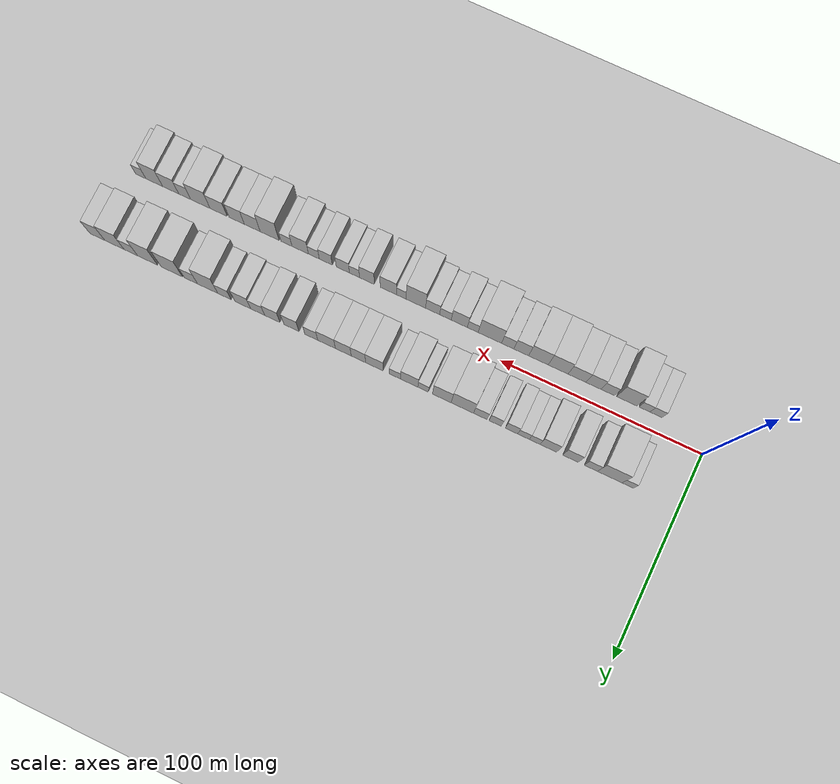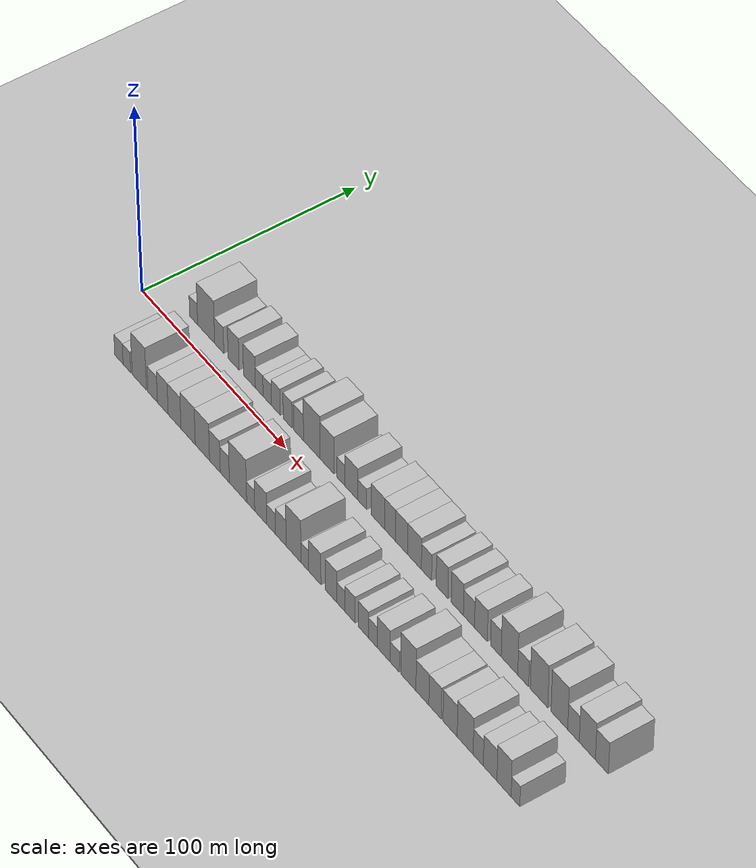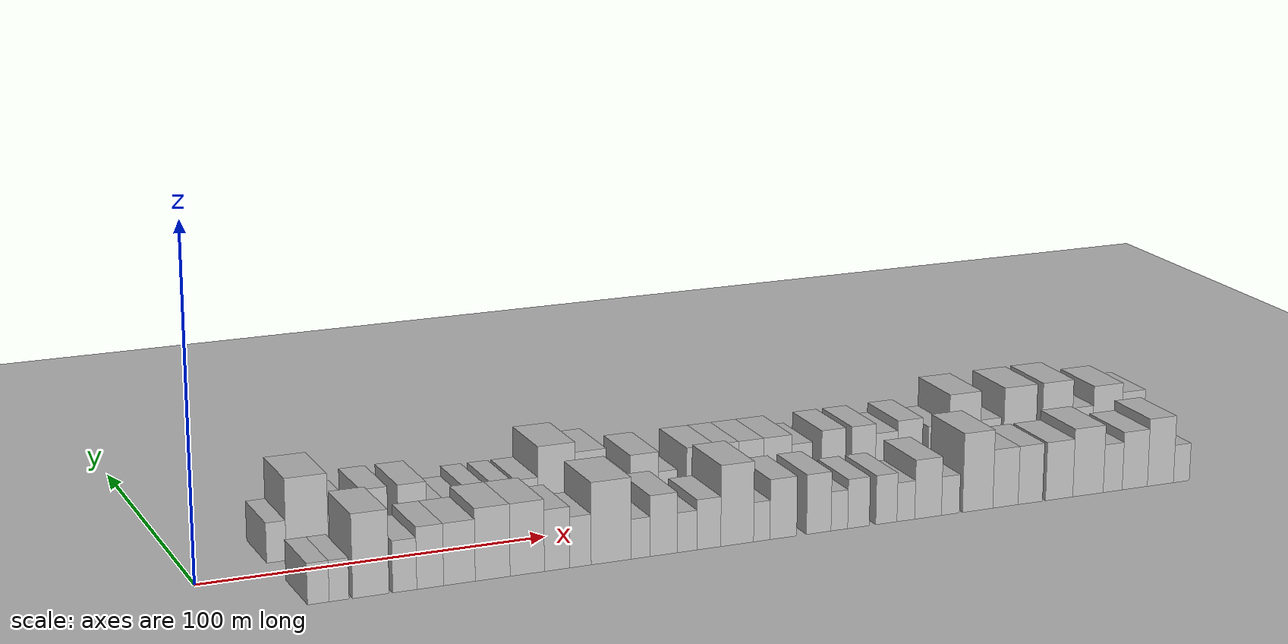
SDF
<?xml version="1.0" encoding="utf-8"?>

<sdf version="1.6">

   <world name="default">

      <gui fullscreen="0">

         <camera name="user_camera">

            <pose>-15 0 4.57585 0 0 0</pose>

            <view_controller>orbit</view_controller>

         </camera>

      </gui>

      <scene>

         <sky>

           <clouds>

             <speed>12</speed>

           </clouds>

         </sky>

         <ambient>0.4 0.4 0.4 1</ambient>

         <background>0.7 0.7 0.7 1</background>

         <shadows>1</shadows>

      </scene>

      <gravity>0 0 -9.8066</gravity>

      <magnetic_field>6e-06 2.3e-05 -4.2e-05</magnetic_field>

      <physics default="0" name="default_physics" type="ode">

         <ode>

            <solver>

               <type>quick</type>

               <iters>10</iters>

               <sor>1.0</sor>

               <use_dynamic_moi_rescaling>0</use_dynamic_moi_rescaling>

            </solver>

            <constraints>

               <cfm>0</cfm>

               <erp>0.2</erp>

               <contact_max_correcting_vel>100</contact_max_correcting_vel>

               <contact_surface_layer>0.001</contact_surface_layer>

            </constraints>

         </ode>

         <max_step_size>0.004</max_step_size>

         <real_time_factor>1</real_time_factor>

         <real_time_update_rate>250</real_time_update_rate>

      </physics>

      <light name="sun" type="directional">

         <cast_shadows>1</cast_shadows>

         <pose>0 0 10 0 0 0</pose>

         <diffuse>0.8 0.8 0.8 1</diffuse>

         <specular>0.2 0.2 0.2 1</specular>

         <attenuation>

            <range>1000</range>

            <constant>0.9</constant>

            <linear>0.01</linear>

            <quadratic>0.001</quadratic>

         </attenuation>

         <direction>-0.5 0.1 -0.9</direction>

      </light>

      <include>

         <name>ground_plane_1</name>

         <uri>model://HANNAS_ground_plane</uri>

         <pose>0 0 0  0 0 0</pose>

      </include>

      <include>

         <name>ground_plane_2</name>

         <uri>model://HANNAS_ground_plane</uri>

         <pose>100 0 0  0 0 0</pose>

      </include>

      <model name="building_1">

         <static>1</static>

         <pose frame="">24.7903 17.5000 0 0.000000 0.000000 1.570796</pose>

         <link name="link">

            <pose frame="">0 0 6.00 0 0 0</pose>

            <collision name="collision">

               <geometry>

                  <box>

                     <size>20.0000 5.5807 12.0000</size>

                  </box>

               </geometry>

               <max_contacts>10</max_contacts>

               <surface>

                  <contact>

                     <ode/>

                  </contact>

                  <bounce/>

                  <friction>

                     <torsional>

                        <ode/>

                     </torsional>

                     <ode/>

                  </friction>

               </surface>

            </collision>

            <visual name="visual">

               <cast_shadows>0</cast_shadows>

               <geometry>

                  <box>

                     <size>20.0000 5.5807 12.0000</size>

                  </box>

               </geometry>

               <material>

                  <script>

                     <uri>model://HANNAS_wall/materials/scripts</uri>

                     <uri>model://HANNAS_wall/materials/textures</uri>

                     <name>vrc/HANNAS_wall</name>

                  </script>

               </material>

            </visual>

            <self_collide>0</self_collide>

            <enable_wind>0</enable_wind>

            <kinematic>0</kinematic>

         </link>

      </model>

      <model name="building_2">

         <static>1</static>

         <pose frame="">33.5785 17.5000 0 0.000000 0.000000 1.570796</pose>

         <link name="link">

            <pose frame="">0 0 12.00 0 0 0</pose>

            <collision name="collision">

               <geometry>

                  <box>

                     <size>20.0000 11.9957 24.0000</size>

                  </box>

               </geometry>

               <max_contacts>10</max_contacts>

               <surface>

                  <contact>

                     <ode/>

                  </contact>

                  <bounce/>

                  <friction>

                     <torsional>

                        <ode/>

                     </torsional>

                     <ode/>

                  </friction>

               </surface>

            </collision>

            <visual name="visual">

               <cast_shadows>0</cast_shadows>

               <geometry>

                  <box>

                     <size>20.0000 11.9957 24.0000</size>

                  </box>

               </geometry>

               <material>

                  <script>

                     <uri>model://HANNAS_wall/materials/scripts</uri>

                     <uri>model://HANNAS_wall/materials/textures</uri>

                     <name>vrc/HANNAS_wall</name>

                  </script>

               </material>

            </visual>

            <self_collide>0</self_collide>

            <enable_wind>0</enable_wind>

            <kinematic>0</kinematic>

         </link>

      </model>

      <model name="building_3">

         <static>1</static>

         <pose frame="">42.7927 17.5000 0 0.000000 0.000000 1.570796</pose>

         <link name="link">

            <pose frame="">0 0 7.50 0 0 0</pose>

            <collision name="collision">

               <geometry>

                  <box>

                     <size>20.0000 6.4326 15.0000</size>

                  </box>

               </geometry>

               <max_contacts>10</max_contacts>

               <surface>

                  <contact>

                     <ode/>

                  </contact>

                  <bounce/>

                  <friction>

                     <torsional>

                        <ode/>

                     </torsional>

                     <ode/>

                  </friction>

               </surface>

            </collision>

            <visual name="visual">

               <cast_shadows>0</cast_shadows>

               <geometry>

                  <box>

                     <size>20.0000 6.4326 15.0000</size>

                  </box>

               </geometry>

               <material>

                  <script>

                     <uri>model://HANNAS_wall/materials/scripts</uri>

                     <uri>model://HANNAS_wall/materials/textures</uri>

                     <name>vrc/HANNAS_wall</name>

                  </script>

               </material>

            </visual>

            <self_collide>0</self_collide>

            <enable_wind>0</enable_wind>

            <kinematic>0</kinematic>

         </link>

      </model>

      <model name="building_4">

         <static>1</static>

         <pose frame="">52.8391 17.5000 0 0.000000 0.000000 1.570796</pose>

         <link name="link">

            <pose frame="">0 0 9.00 0 0 0</pose>

            <collision name="collision">

               <geometry>

                  <box>

                     <size>20.0000 7.6602 18.0000</size>

                  </box>

               </geometry>

               <max_contacts>10</max_contacts>

               <surface>

                  <contact>

                     <ode/>

                  </contact>

                  <bounce/>

                  <friction>

                     <torsional>

                        <ode/>

                     </torsional>

                     <ode/>

                  </friction>

               </surface>

            </collision>

            <visual name="visual">

               <cast_shadows>0</cast_shadows>

               <geometry>

                  <box>

                     <size>20.0000 7.6602 18.0000</size>

                  </box>

               </geometry>

               <material>

                  <script>

                     <uri>model://HANNAS_wall/materials/scripts</uri>

                     <uri>model://HANNAS_wall/materials/textures</uri>

                     <name>vrc/HANNAS_wall</name>

                  </script>

               </material>

            </visual>

            <self_collide>0</self_collide>

            <enable_wind>0</enable_wind>

            <kinematic>0</kinematic>

         </link>

      </model>

      <model name="building_5">

         <static>1</static>

         <pose frame="">63.7903 17.5000 0 0.000000 0.000000 1.570796</pose>

         <link name="link">

            <pose frame="">0 0 9.00 0 0 0</pose>

            <collision name="collision">

               <geometry>

                  <box>

                     <size>20.0000 8.2422 18.0000</size>

                  </box>

               </geometry>

               <max_contacts>10</max_contacts>

               <surface>

                  <contact>

                     <ode/>

                  </contact>

                  <bounce/>

                  <friction>

                     <torsional>

                        <ode/>

                     </torsional>

                     <ode/>

                  </friction>

               </surface>

            </collision>

            <visual name="visual">

               <cast_shadows>0</cast_shadows>

               <geometry>

                  <box>

                     <size>20.0000 8.2422 18.0000</size>

                  </box>

               </geometry>

               <material>

                  <script>

                     <uri>model://HANNAS_wall/materials/scripts</uri>

                     <uri>model://HANNAS_wall/materials/textures</uri>

                     <name>vrc/HANNAS_wall</name>

                  </script>

               </material>

            </visual>

            <self_collide>0</self_collide>

            <enable_wind>0</enable_wind>

            <kinematic>0</kinematic>

         </link>

      </model>

      <model name="building_6">

         <static>1</static>

         <pose frame="">70.5453 17.5000 0 0.000000 0.000000 1.570796</pose>

         <link name="link">

            <pose frame="">0 0 6.00 0 0 0</pose>

            <collision name="collision">

               <geometry>

                  <box>

                     <size>20.0000 5.2677 12.0000</size>

                  </box>

               </geometry>

               <max_contacts>10</max_contacts>

               <surface>

                  <contact>

                     <ode/>

                  </contact>

                  <bounce/>

                  <friction>

                     <torsional>

                        <ode/>

                     </torsional>

                     <ode/>

                  </friction>

               </surface>

            </collision>

            <visual name="visual">

               <cast_shadows>0</cast_shadows>

               <geometry>

                  <box>

                     <size>20.0000 5.2677 12.0000</size>

                  </box>

               </geometry>

               <material>

                  <script>

                     <uri>model://HANNAS_wall/materials/scripts</uri>

                     <uri>model://HANNAS_wall/materials/textures</uri>

                     <name>vrc/HANNAS_wall</name>

                  </script>

               </material>

            </visual>

            <self_collide>0</self_collide>

            <enable_wind>0</enable_wind>

            <kinematic>0</kinematic>

         </link>

      </model>

      <model name="building_7">

         <static>1</static>

         <pose frame="">76.0698 17.5000 0 0.000000 0.000000 1.570796</pose>

         <link name="link">

            <pose frame="">0 0 6.00 0 0 0</pose>

            <collision name="collision">

               <geometry>

                  <box>

                     <size>20.0000 5.7813 12.0000</size>

                  </box>

               </geometry>

               <max_contacts>10</max_contacts>

               <surface>

                  <contact>

                     <ode/>

                  </contact>

                  <bounce/>

                  <friction>

                     <torsional>

                        <ode/>

                     </torsional>

                     <ode/>

                  </friction>

               </surface>

            </collision>

            <visual name="visual">

               <cast_shadows>0</cast_shadows>

               <geometry>

                  <box>

                     <size>20.0000 5.7813 12.0000</size>

                  </box>

               </geometry>

               <material>

                  <script>

                     <uri>model://HANNAS_wall/materials/scripts</uri>

                     <uri>model://HANNAS_wall/materials/textures</uri>

                     <name>vrc/HANNAS_wall</name>

                  </script>

               </material>

            </visual>

            <self_collide>0</self_collide>

            <enable_wind>0</enable_wind>

            <kinematic>0</kinematic>

         </link>

      </model>

      <model name="building_8">

         <static>1</static>

         <pose frame="">82.0250 17.5000 0 0.000000 0.000000 1.570796</pose>

         <link name="link">

            <pose frame="">0 0 7.50 0 0 0</pose>

            <collision name="collision">

               <geometry>

                  <box>

                     <size>20.0000 6.1293 15.0000</size>

                  </box>

               </geometry>

               <max_contacts>10</max_contacts>

               <surface>

                  <contact>

                     <ode/>

                  </contact>

                  <bounce/>

                  <friction>

                     <torsional>

                        <ode/>

                     </torsional>

                     <ode/>

                  </friction>

               </surface>

            </collision>

            <visual name="visual">

               <cast_shadows>0</cast_shadows>

               <geometry>

                  <box>

                     <size>20.0000 6.1293 15.0000</size>

                  </box>

               </geometry>

               <material>

                  <script>

                     <uri>model://HANNAS_wall/materials/scripts</uri>

                     <uri>model://HANNAS_wall/materials/textures</uri>

                     <name>vrc/HANNAS_wall</name>

                  </script>

               </material>

            </visual>

            <self_collide>0</self_collide>

            <enable_wind>0</enable_wind>

            <kinematic>0</kinematic>

         </link>

      </model>

      <model name="building_9">

         <static>1</static>

         <pose frame="">90.1376 17.5000 0 0.000000 0.000000 1.570796</pose>

         <link name="link">

            <pose frame="">0 0 7.50 0 0 0</pose>

            <collision name="collision">

               <geometry>

                  <box>

                     <size>20.0000 6.0958 15.0000</size>

                  </box>

               </geometry>

               <max_contacts>10</max_contacts>

               <surface>

                  <contact>

                     <ode/>

                  </contact>

                  <bounce/>

                  <friction>

                     <torsional>

                        <ode/>

                     </torsional>

                     <ode/>

                  </friction>

               </surface>

            </collision>

            <visual name="visual">

               <cast_shadows>0</cast_shadows>

               <geometry>

                  <box>

                     <size>20.0000 6.0958 15.0000</size>

                  </box>

               </geometry>

               <material>

                  <script>

                     <uri>model://HANNAS_wall/materials/scripts</uri>

                     <uri>model://HANNAS_wall/materials/textures</uri>

                     <name>vrc/HANNAS_wall</name>

                  </script>

               </material>

            </visual>

            <self_collide>0</self_collide>

            <enable_wind>0</enable_wind>

            <kinematic>0</kinematic>

         </link>

      </model>

      <model name="building_10">

         <static>1</static>

         <pose frame="">97.5536 17.5000 0 0.000000 0.000000 1.570796</pose>

         <link name="link">

            <pose frame="">0 0 7.50 0 0 0</pose>

            <collision name="collision">

               <geometry>

                  <box>

                     <size>20.0000 6.7362 15.0000</size>

                  </box>

               </geometry>

               <max_contacts>10</max_contacts>

               <surface>

                  <contact>

                     <ode/>

                  </contact>

                  <bounce/>

                  <friction>

                     <torsional>

                        <ode/>

                     </torsional>

                     <ode/>

                  </friction>

               </surface>

            </collision>

            <visual name="visual">

               <cast_shadows>0</cast_shadows>

               <geometry>

                  <box>

                     <size>20.0000 6.7362 15.0000</size>

                  </box>

               </geometry>

               <material>

                  <script>

                     <uri>model://HANNAS_wall/materials/scripts</uri>

                     <uri>model://HANNAS_wall/materials/textures</uri>

                     <name>vrc/HANNAS_wall</name>

                  </script>

               </material>

            </visual>

            <self_collide>0</self_collide>

            <enable_wind>0</enable_wind>

            <kinematic>0</kinematic>

         </link>

      </model>

      <model name="building_11">

         <static>1</static>

         <pose frame="">106.5154 17.5000 0 0.000000 0.000000 1.570796</pose>

         <link name="link">

            <pose frame="">0 0 12.00 0 0 0</pose>

            <collision name="collision">

               <geometry>

                  <box>

                     <size>20.0000 11.1872 24.0000</size>

                  </box>

               </geometry>

               <max_contacts>10</max_contacts>

               <surface>

                  <contact>

                     <ode/>

                  </contact>

                  <bounce/>

                  <friction>

                     <torsional>

                        <ode/>

                     </torsional>

                     <ode/>

                  </friction>

               </surface>

            </collision>

            <visual name="visual">

               <cast_shadows>0</cast_shadows>

               <geometry>

                  <box>

                     <size>20.0000 11.1872 24.0000</size>

                  </box>

               </geometry>

               <material>

                  <script>

                     <uri>model://HANNAS_wall/materials/scripts</uri>

                     <uri>model://HANNAS_wall/materials/textures</uri>

                     <name>vrc/HANNAS_wall</name>

                  </script>

               </material>

            </visual>

            <self_collide>0</self_collide>

            <enable_wind>0</enable_wind>

            <kinematic>0</kinematic>

         </link>

      </model>

      <model name="building_12">

         <static>1</static>

         <pose frame="">116.8096 17.5000 0 0.000000 0.000000 1.570796</pose>

         <link name="link">

            <pose frame="">0 0 10.50 0 0 0</pose>

            <collision name="collision">

               <geometry>

                  <box>

                     <size>20.0000 9.4012 21.0000</size>

                  </box>

               </geometry>

               <max_contacts>10</max_contacts>

               <surface>

                  <contact>

                     <ode/>

                  </contact>

                  <bounce/>

                  <friction>

                     <torsional>

                        <ode/>

                     </torsional>

                     <ode/>

                  </friction>

               </surface>

            </collision>

            <visual name="visual">

               <cast_shadows>0</cast_shadows>

               <geometry>

                  <box>

                     <size>20.0000 9.4012 21.0000</size>

                  </box>

               </geometry>

               <material>

                  <script>

                     <uri>model://HANNAS_wall/materials/scripts</uri>

                     <uri>model://HANNAS_wall/materials/textures</uri>

                     <name>vrc/HANNAS_wall</name>

                  </script>

               </material>

            </visual>

            <self_collide>0</self_collide>

            <enable_wind>0</enable_wind>

            <kinematic>0</kinematic>

         </link>

      </model>

      <model name="building_13">

         <static>1</static>

         <pose frame="">126.1650 17.5000 0 0.000000 0.000000 1.570796</pose>

         <link name="link">

            <pose frame="">0 0 6.00 0 0 0</pose>

            <collision name="collision">

               <geometry>

                  <box>

                     <size>20.0000 5.3096 12.0000</size>

                  </box>

               </geometry>

               <max_contacts>10</max_contacts>

               <surface>

                  <contact>

                     <ode/>

                  </contact>

                  <bounce/>

                  <friction>

                     <torsional>

                        <ode/>

                     </torsional>

                     <ode/>

                  </friction>

               </surface>

            </collision>

            <visual name="visual">

               <cast_shadows>0</cast_shadows>

               <geometry>

                  <box>

                     <size>20.0000 5.3096 12.0000</size>

                  </box>

               </geometry>

               <material>

                  <script>

                     <uri>model://HANNAS_wall/materials/scripts</uri>

                     <uri>model://HANNAS_wall/materials/textures</uri>

                     <name>vrc/HANNAS_wall</name>

                  </script>

               </material>

            </visual>

            <self_collide>0</self_collide>

            <enable_wind>0</enable_wind>

            <kinematic>0</kinematic>

         </link>

      </model>

      <model name="building_14">

         <static>1</static>

         <pose frame="">133.2115 17.5000 0 0.000000 0.000000 1.570796</pose>

         <link name="link">

            <pose frame="">0 0 9.00 0 0 0</pose>

            <collision name="collision">

               <geometry>

                  <box>

                     <size>20.0000 8.7833 18.0000</size>

                  </box>

               </geometry>

               <max_contacts>10</max_contacts>

               <surface>

                  <contact>

                     <ode/>

                  </contact>

                  <bounce/>

                  <friction>

                     <torsional>

                        <ode/>

                     </torsional>

                     <ode/>

                  </friction>

               </surface>

            </collision>

            <visual name="visual">

               <cast_shadows>0</cast_shadows>

               <geometry>

                  <box>

                     <size>20.0000 8.7833 18.0000</size>

                  </box>

               </geometry>

               <material>

                  <script>

                     <uri>model://HANNAS_wall/materials/scripts</uri>

                     <uri>model://HANNAS_wall/materials/textures</uri>

                     <name>vrc/HANNAS_wall</name>

                  </script>

               </material>

            </visual>

            <self_collide>0</self_collide>

            <enable_wind>0</enable_wind>

            <kinematic>0</kinematic>

         </link>

      </model>

      <model name="building_15">

         <static>1</static>

         <pose frame="">140.4692 17.5000 0 0.000000 0.000000 1.570796</pose>

         <link name="link">

            <pose frame="">0 0 6.00 0 0 0</pose>

            <collision name="collision">

               <geometry>

                  <box>

                     <size>20.0000 5.7321 12.0000</size>

                  </box>

               </geometry>

               <max_contacts>10</max_contacts>

               <surface>

                  <contact>

                     <ode/>

                  </contact>

                  <bounce/>

                  <friction>

                     <torsional>

                        <ode/>

                     </torsional>

                     <ode/>

                  </friction>

               </surface>

            </collision>

            <visual name="visual">

               <cast_shadows>0</cast_shadows>

               <geometry>

                  <box>

                     <size>20.0000 5.7321 12.0000</size>

                  </box>

               </geometry>

               <material>

                  <script>

                     <uri>model://HANNAS_wall/materials/scripts</uri>

                     <uri>model://HANNAS_wall/materials/textures</uri>

                     <name>vrc/HANNAS_wall</name>

                  </script>

               </material>

            </visual>

            <self_collide>0</self_collide>

            <enable_wind>0</enable_wind>

            <kinematic>0</kinematic>

         </link>

      </model>

      <model name="building_16">

         <static>1</static>

         <pose frame="">150.7560 17.5000 0 0.000000 0.000000 1.570796</pose>

         <link name="link">

            <pose frame="">0 0 9.00 0 0 0</pose>

            <collision name="collision">

               <geometry>

                  <box>

                     <size>20.0000 8.8416 18.0000</size>

                  </box>

               </geometry>

               <max_contacts>10</max_contacts>

               <surface>

                  <contact>

                     <ode/>

                  </contact>

                  <bounce/>

                  <friction>

                     <torsional>

                        <ode/>

                     </torsional>

                     <ode/>

                  </friction>

               </surface>

            </collision>

            <visual name="visual">

               <cast_shadows>0</cast_shadows>

               <geometry>

                  <box>

                     <size>20.0000 8.8416 18.0000</size>

                  </box>

               </geometry>

               <material>

                  <script>

                     <uri>model://HANNAS_wall/materials/scripts</uri>

                     <uri>model://HANNAS_wall/materials/textures</uri>

                     <name>vrc/HANNAS_wall</name>

                  </script>

               </material>

            </visual>

            <self_collide>0</self_collide>

            <enable_wind>0</enable_wind>

            <kinematic>0</kinematic>

         </link>

      </model>

      <model name="building_17">

         <static>1</static>

         <pose frame="">158.8325 17.5000 0 0.000000 0.000000 1.570796</pose>

         <link name="link">

            <pose frame="">0 0 9.00 0 0 0</pose>

            <collision name="collision">

               <geometry>

                  <box>

                     <size>20.0000 7.3114 18.0000</size>

                  </box>

               </geometry>

               <max_contacts>10</max_contacts>

               <surface>

                  <contact>

                     <ode/>

                  </contact>

                  <bounce/>

                  <friction>

                     <torsional>

                        <ode/>

                     </torsional>

                     <ode/>

                  </friction>

               </surface>

            </collision>

            <visual name="visual">

               <cast_shadows>0</cast_shadows>

               <geometry>

                  <box>

                     <size>20.0000 7.3114 18.0000</size>

                  </box>

               </geometry>

               <material>

                  <script>

                     <uri>model://HANNAS_wall/materials/scripts</uri>

                     <uri>model://HANNAS_wall/materials/textures</uri>

                     <name>vrc/HANNAS_wall</name>

                  </script>

               </material>

            </visual>

            <self_collide>0</self_collide>

            <enable_wind>0</enable_wind>

            <kinematic>0</kinematic>

         </link>

      </model>

      <model name="building_18">

         <static>1</static>

         <pose frame="">166.4875 17.5000 0 0.000000 0.000000 1.570796</pose>

         <link name="link">

            <pose frame="">0 0 9.00 0 0 0</pose>

            <collision name="collision">

               <geometry>

                  <box>

                     <size>20.0000 7.9986 18.0000</size>

                  </box>

               </geometry>

               <max_contacts>10</max_contacts>

               <surface>

                  <contact>

                     <ode/>

                  </contact>

                  <bounce/>

                  <friction>

                     <torsional>

                        <ode/>

                     </torsional>

                     <ode/>

                  </friction>

               </surface>

            </collision>

            <visual name="visual">

               <cast_shadows>0</cast_shadows>

               <geometry>

                  <box>

                     <size>20.0000 7.9986 18.0000</size>

                  </box>

               </geometry>

               <material>

                  <script>

                     <uri>model://HANNAS_wall/materials/scripts</uri>

                     <uri>model://HANNAS_wall/materials/textures</uri>

                     <name>vrc/HANNAS_wall</name>

                  </script>

               </material>

            </visual>

            <self_collide>0</self_collide>

            <enable_wind>0</enable_wind>

            <kinematic>0</kinematic>

         </link>

      </model>

      <model name="building_19">

         <static>1</static>

         <pose frame="">174.9716 17.5000 0 0.000000 0.000000 1.570796</pose>

         <link name="link">

            <pose frame="">0 0 9.00 0 0 0</pose>

            <collision name="collision">

               <geometry>

                  <box>

                     <size>20.0000 8.9696 18.0000</size>

                  </box>

               </geometry>

               <max_contacts>10</max_contacts>

               <surface>

                  <contact>

                     <ode/>

                  </contact>

                  <bounce/>

                  <friction>

                     <torsional>

                        <ode/>

                     </torsional>

                     <ode/>

                  </friction>

               </surface>

            </collision>

            <visual name="visual">

               <cast_shadows>0</cast_shadows>

               <geometry>

                  <box>

                     <size>20.0000 8.9696 18.0000</size>

                  </box>

               </geometry>

               <material>

                  <script>

                     <uri>model://HANNAS_wall/materials/scripts</uri>

                     <uri>model://HANNAS_wall/materials/textures</uri>

                     <name>vrc/HANNAS_wall</name>

                  </script>

               </material>

            </visual>

            <self_collide>0</self_collide>

            <enable_wind>0</enable_wind>

            <kinematic>0</kinematic>

         </link>

      </model>

      <model name="building_20">

         <static>1</static>

         <pose frame="">182.7605 17.5000 0 0.000000 0.000000 1.570796</pose>

         <link name="link">

            <pose frame="">0 0 7.50 0 0 0</pose>

            <collision name="collision">

               <geometry>

                  <box>

                     <size>20.0000 6.6081 15.0000</size>

                  </box>

               </geometry>

               <max_contacts>10</max_contacts>

               <surface>

                  <contact>

                     <ode/>

                  </contact>

                  <bounce/>

                  <friction>

                     <torsional>

                        <ode/>

                     </torsional>

                     <ode/>

                  </friction>

               </surface>

            </collision>

            <visual name="visual">

               <cast_shadows>0</cast_shadows>

               <geometry>

                  <box>

                     <size>20.0000 6.6081 15.0000</size>

                  </box>

               </geometry>

               <material>

                  <script>

                     <uri>model://HANNAS_wall/materials/scripts</uri>

                     <uri>model://HANNAS_wall/materials/textures</uri>

                     <name>vrc/HANNAS_wall</name>

                  </script>

               </material>

            </visual>

            <self_collide>0</self_collide>

            <enable_wind>0</enable_wind>

            <kinematic>0</kinematic>

         </link>

      </model>

      <model name="building_21">

         <static>1</static>

         <pose frame="">192.9308 17.5000 0 0.000000 0.000000 1.570796</pose>

         <link name="link">

            <pose frame="">0 0 9.00 0 0 0</pose>

            <collision name="collision">

               <geometry>

                  <box>

                     <size>20.0000 7.7326 18.0000</size>

                  </box>

               </geometry>

               <max_contacts>10</max_contacts>

               <surface>

                  <contact>

                     <ode/>

                  </contact>

                  <bounce/>

                  <friction>

                     <torsional>

                        <ode/>

                     </torsional>

                     <ode/>

                  </friction>

               </surface>

            </collision>

            <visual name="visual">

               <cast_shadows>0</cast_shadows>

               <geometry>

                  <box>

                     <size>20.0000 7.7326 18.0000</size>

                  </box>

               </geometry>

               <material>

                  <script>

                     <uri>model://HANNAS_wall/materials/scripts</uri>

                     <uri>model://HANNAS_wall/materials/textures</uri>

                     <name>vrc/HANNAS_wall</name>

                  </script>

               </material>

            </visual>

            <self_collide>0</self_collide>

            <enable_wind>0</enable_wind>

            <kinematic>0</kinematic>

         </link>

      </model>

      <model name="building_22">

         <static>1</static>

         <pose frame="">202.7216 17.5000 0 0.000000 0.000000 1.570796</pose>

         <link name="link">

            <pose frame="">0 0 9.00 0 0 0</pose>

            <collision name="collision">

               <geometry>

                  <box>

                     <size>20.0000 7.8489 18.0000</size>

                  </box>

               </geometry>

               <max_contacts>10</max_contacts>

               <surface>

                  <contact>

                     <ode/>

                  </contact>

                  <bounce/>

                  <friction>

                     <torsional>

                        <ode/>

                     </torsional>

                     <ode/>

                  </friction>

               </surface>

            </collision>

            <visual name="visual">

               <cast_shadows>0</cast_shadows>

               <geometry>

                  <box>

                     <size>20.0000 7.8489 18.0000</size>

                  </box>

               </geometry>

               <material>

                  <script>

                     <uri>model://HANNAS_wall/materials/scripts</uri>

                     <uri>model://HANNAS_wall/materials/textures</uri>

                     <name>vrc/HANNAS_wall</name>

                  </script>

               </material>

            </visual>

            <self_collide>0</self_collide>

            <enable_wind>0</enable_wind>

            <kinematic>0</kinematic>

         </link>

      </model>

      <model name="building_23">

         <static>1</static>

         <pose frame="">210.2408 17.5000 0 0.000000 0.000000 1.570796</pose>

         <link name="link">

            <pose frame="">0 0 7.50 0 0 0</pose>

            <collision name="collision">

               <geometry>

                  <box>

                     <size>20.0000 7.1895 15.0000</size>

                  </box>

               </geometry>

               <max_contacts>10</max_contacts>

               <surface>

                  <contact>

                     <ode/>

                  </contact>

                  <bounce/>

                  <friction>

                     <torsional>

                        <ode/>

                     </torsional>

                     <ode/>

                  </friction>

               </surface>

            </collision>

            <visual name="visual">

               <cast_shadows>0</cast_shadows>

               <geometry>

                  <box>

                     <size>20.0000 7.1895 15.0000</size>

                  </box>

               </geometry>

               <material>

                  <script>

                     <uri>model://HANNAS_wall/materials/scripts</uri>

                     <uri>model://HANNAS_wall/materials/textures</uri>

                     <name>vrc/HANNAS_wall</name>

                  </script>

               </material>

            </visual>

            <self_collide>0</self_collide>

            <enable_wind>0</enable_wind>

            <kinematic>0</kinematic>

         </link>

      </model>

      <model name="building_24">

         <static>1</static>

         <pose frame="">217.9297 17.5000 0 0.000000 0.000000 1.570796</pose>

         <link name="link">

            <pose frame="">0 0 9.00 0 0 0</pose>

            <collision name="collision">

               <geometry>

                  <box>

                     <size>20.0000 8.1882 18.0000</size>

                  </box>

               </geometry>

               <max_contacts>10</max_contacts>

               <surface>

                  <contact>

                     <ode/>

                  </contact>

                  <bounce/>

                  <friction>

                     <torsional>

                        <ode/>

                     </torsional>

                     <ode/>

                  </friction>

               </surface>

            </collision>

            <visual name="visual">

               <cast_shadows>0</cast_shadows>

               <geometry>

                  <box>

                     <size>20.0000 8.1882 18.0000</size>

                  </box>

               </geometry>

               <material>

                  <script>

                     <uri>model://HANNAS_wall/materials/scripts</uri>

                     <uri>model://HANNAS_wall/materials/textures</uri>

                     <name>vrc/HANNAS_wall</name>

                  </script>

               </material>

            </visual>

            <self_collide>0</self_collide>

            <enable_wind>0</enable_wind>

            <kinematic>0</kinematic>

         </link>

      </model>

      <model name="building_25">

         <static>1</static>

         <pose frame="">227.4332 17.5000 0 0.000000 0.000000 1.570796</pose>

         <link name="link">

            <pose frame="">0 0 7.50 0 0 0</pose>

            <collision name="collision">

               <geometry>

                  <box>

                     <size>20.0000 6.8190 15.0000</size>

                  </box>

               </geometry>

               <max_contacts>10</max_contacts>

               <surface>

                  <contact>

                     <ode/>

                  </contact>

                  <bounce/>

                  <friction>

                     <torsional>

                        <ode/>

                     </torsional>

                     <ode/>

                  </friction>

               </surface>

            </collision>

            <visual name="visual">

               <cast_shadows>0</cast_shadows>

               <geometry>

                  <box>

                     <size>20.0000 6.8190 15.0000</size>

                  </box>

               </geometry>

               <material>

                  <script>

                     <uri>model://HANNAS_wall/materials/scripts</uri>

                     <uri>model://HANNAS_wall/materials/textures</uri>

                     <name>vrc/HANNAS_wall</name>

                  </script>

               </material>

            </visual>

            <self_collide>0</self_collide>

            <enable_wind>0</enable_wind>

            <kinematic>0</kinematic>

         </link>

      </model>

      <model name="building_26">

         <static>1</static>

         <pose frame="">236.1009 17.5000 0 0.000000 0.000000 1.570796</pose>

         <link name="link">

            <pose frame="">0 0 12.00 0 0 0</pose>

            <collision name="collision">

               <geometry>

                  <box>

                     <size>20.0000 10.5164 24.0000</size>

                  </box>

               </geometry>

               <max_contacts>10</max_contacts>

               <surface>

                  <contact>

                     <ode/>

                  </contact>

                  <bounce/>

                  <friction>

                     <torsional>

                        <ode/>

                     </torsional>

                     <ode/>

                  </friction>

               </surface>

            </collision>

            <visual name="visual">

               <cast_shadows>0</cast_shadows>

               <geometry>

                  <box>

                     <size>20.0000 10.5164 24.0000</size>

                  </box>

               </geometry>

               <material>

                  <script>

                     <uri>model://HANNAS_wall/materials/scripts</uri>

                     <uri>model://HANNAS_wall/materials/textures</uri>

                     <name>vrc/HANNAS_wall</name>

                  </script>

               </material>

            </visual>

            <self_collide>0</self_collide>

            <enable_wind>0</enable_wind>

            <kinematic>0</kinematic>

         </link>

      </model>

      <model name="building_27">

         <static>1</static>

         <pose frame="">244.7884 17.5000 0 0.000000 0.000000 1.570796</pose>

         <link name="link">

            <pose frame="">0 0 7.50 0 0 0</pose>

            <collision name="collision">

               <geometry>

                  <box>

                     <size>20.0000 6.8587 15.0000</size>

                  </box>

               </geometry>

               <max_contacts>10</max_contacts>

               <surface>

                  <contact>

                     <ode/>

                  </contact>

                  <bounce/>

                  <friction>

                     <torsional>

                        <ode/>

                     </torsional>

                     <ode/>

                  </friction>

               </surface>

            </collision>

            <visual name="visual">

               <cast_shadows>0</cast_shadows>

               <geometry>

                  <box>

                     <size>20.0000 6.8587 15.0000</size>

                  </box>

               </geometry>

               <material>

                  <script>

                     <uri>model://HANNAS_wall/materials/scripts</uri>

                     <uri>model://HANNAS_wall/materials/textures</uri>

                     <name>vrc/HANNAS_wall</name>

                  </script>

               </material>

            </visual>

            <self_collide>0</self_collide>

            <enable_wind>0</enable_wind>

            <kinematic>0</kinematic>

         </link>

      </model>

      <model name="building_28">

         <static>1</static>

         <pose frame="">254.7375 17.5000 0 0.000000 0.000000 1.570796</pose>

         <link name="link">

            <pose frame="">0 0 12.00 0 0 0</pose>

            <collision name="collision">

               <geometry>

                  <box>

                     <size>20.0000 11.0396 24.0000</size>

                  </box>

               </geometry>

               <max_contacts>10</max_contacts>

               <surface>

                  <contact>

                     <ode/>

                  </contact>

                  <bounce/>

                  <friction>

                     <torsional>

                        <ode/>

                     </torsional>

                     <ode/>

                  </friction>

               </surface>

            </collision>

            <visual name="visual">

               <cast_shadows>0</cast_shadows>

               <geometry>

                  <box>

                     <size>20.0000 11.0396 24.0000</size>

                  </box>

               </geometry>

               <material>

                  <script>

                     <uri>model://HANNAS_wall/materials/scripts</uri>

                     <uri>model://HANNAS_wall/materials/textures</uri>

                     <name>vrc/HANNAS_wall</name>

                  </script>

               </material>

            </visual>

            <self_collide>0</self_collide>

            <enable_wind>0</enable_wind>

            <kinematic>0</kinematic>

         </link>

      </model>

      <model name="building_29">

         <static>1</static>

         <pose frame="">267.4569 17.5000 0 0.000000 0.000000 1.570796</pose>

         <link name="link">

            <pose frame="">0 0 12.00 0 0 0</pose>

            <collision name="collision">

               <geometry>

                  <box>

                     <size>20.0000 10.3992 24.0000</size>

                  </box>

               </geometry>

               <max_contacts>10</max_contacts>

               <surface>

                  <contact>

                     <ode/>

                  </contact>

                  <bounce/>

                  <friction>

                     <torsional>

                        <ode/>

                     </torsional>

                     <ode/>

                  </friction>

               </surface>

            </collision>

            <visual name="visual">

               <cast_shadows>0</cast_shadows>

               <geometry>

                  <box>

                     <size>20.0000 10.3992 24.0000</size>

                  </box>

               </geometry>

               <material>

                  <script>

                     <uri>model://HANNAS_wall/materials/scripts</uri>

                     <uri>model://HANNAS_wall/materials/textures</uri>

                     <name>vrc/HANNAS_wall</name>

                  </script>

               </material>

            </visual>

            <self_collide>0</self_collide>

            <enable_wind>0</enable_wind>

            <kinematic>0</kinematic>

         </link>

      </model>

      <model name="building_30">

         <static>1</static>

         <pose frame="">276.2368 17.5000 0 0.000000 0.000000 1.570796</pose>

         <link name="link">

            <pose frame="">0 0 7.50 0 0 0</pose>

            <collision name="collision">

               <geometry>

                  <box>

                     <size>20.0000 7.1605 15.0000</size>

                  </box>

               </geometry>

               <max_contacts>10</max_contacts>

               <surface>

                  <contact>

                     <ode/>

                  </contact>

                  <bounce/>

                  <friction>

                     <torsional>

                        <ode/>

                     </torsional>

                     <ode/>

                  </friction>

               </surface>

            </collision>

            <visual name="visual">

               <cast_shadows>0</cast_shadows>

               <geometry>

                  <box>

                     <size>20.0000 7.1605 15.0000</size>

                  </box>

               </geometry>

               <material>

                  <script>

                     <uri>model://HANNAS_wall/materials/scripts</uri>

                     <uri>model://HANNAS_wall/materials/textures</uri>

                     <name>vrc/HANNAS_wall</name>

                  </script>

               </material>

            </visual>

            <self_collide>0</self_collide>

            <enable_wind>0</enable_wind>

            <kinematic>0</kinematic>

         </link>

      </model>

      <model name="building_31">

         <static>1</static>

         <pose frame="">284.8316 17.5000 0 0.000000 0.000000 1.570796</pose>

         <link name="link">

            <pose frame="">0 0 10.50 0 0 0</pose>

            <collision name="collision">

               <geometry>

                  <box>

                     <size>20.0000 10.0290 21.0000</size>

                  </box>

               </geometry>

               <max_contacts>10</max_contacts>

               <surface>

                  <contact>

                     <ode/>

                  </contact>

                  <bounce/>

                  <friction>

                     <torsional>

                        <ode/>

                     </torsional>

                     <ode/>

                  </friction>

               </surface>

            </collision>

            <visual name="visual">

               <cast_shadows>0</cast_shadows>

               <geometry>

                  <box>

                     <size>20.0000 10.0290 21.0000</size>

                  </box>

               </geometry>

               <material>

                  <script>

                     <uri>model://HANNAS_wall/materials/scripts</uri>

                     <uri>model://HANNAS_wall/materials/textures</uri>

                     <name>vrc/HANNAS_wall</name>

                  </script>

               </material>

            </visual>

            <self_collide>0</self_collide>

            <enable_wind>0</enable_wind>

            <kinematic>0</kinematic>

         </link>

      </model>

      <model name="building_32">

         <static>1</static>

         <pose frame="">293.8147 17.5000 0 0.000000 0.000000 1.570796</pose>

         <link name="link">

            <pose frame="">0 0 9.00 0 0 0</pose>

            <collision name="collision">

               <geometry>

                  <box>

                     <size>20.0000 7.9373 18.0000</size>

                  </box>

               </geometry>

               <max_contacts>10</max_contacts>

               <surface>

                  <contact>

                     <ode/>

                  </contact>

                  <bounce/>

                  <friction>

                     <torsional>

                        <ode/>

                     </torsional>

                     <ode/>

                  </friction>

               </surface>

            </collision>

            <visual name="visual">

               <cast_shadows>0</cast_shadows>

               <geometry>

                  <box>

                     <size>20.0000 7.9373 18.0000</size>

                  </box>

               </geometry>

               <material>

                  <script>

                     <uri>model://HANNAS_wall/materials/scripts</uri>

                     <uri>model://HANNAS_wall/materials/textures</uri>

                     <name>vrc/HANNAS_wall</name>

                  </script>

               </material>

            </visual>

            <self_collide>0</self_collide>

            <enable_wind>0</enable_wind>

            <kinematic>0</kinematic>

         </link>

      </model>

      <model name="building_33">

         <static>1</static>

         <pose frame="">25.9741 -17.5000 0 0.000000 0.000000 1.570796</pose>

         <link name="link">

            <pose frame="">0 0 6.00 0 0 0</pose>

            <collision name="collision">

               <geometry>

                  <box>

                     <size>20.0000 5.9482 12.0000</size>

                  </box>

               </geometry>

               <max_contacts>10</max_contacts>

               <surface>

                  <contact>

                     <ode/>

                  </contact>

                  <bounce/>

                  <friction>

                     <torsional>

                        <ode/>

                     </torsional>

                     <ode/>

                  </friction>

               </surface>

            </collision>

            <visual name="visual">

               <cast_shadows>0</cast_shadows>

               <geometry>

                  <box>

                     <size>20.0000 5.9482 12.0000</size>

                  </box>

               </geometry>

               <material>

                  <script>

                     <uri>model://HANNAS_wall/materials/scripts</uri>

                     <uri>model://HANNAS_wall/materials/textures</uri>

                     <name>vrc/HANNAS_wall</name>

                  </script>

               </material>

            </visual>

            <self_collide>0</self_collide>

            <enable_wind>0</enable_wind>

            <kinematic>0</kinematic>

         </link>

      </model>

      <model name="building_34">

         <static>1</static>

         <pose frame="">31.6685 -17.5000 0 0.000000 0.000000 1.570796</pose>

         <link name="link">

            <pose frame="">0 0 6.00 0 0 0</pose>

            <collision name="collision">

               <geometry>

                  <box>

                     <size>20.0000 5.4406 12.0000</size>

                  </box>

               </geometry>

               <max_contacts>10</max_contacts>

               <surface>

                  <contact>

                     <ode/>

                  </contact>

                  <bounce/>

                  <friction>

                     <torsional>

                        <ode/>

                     </torsional>

                     <ode/>

                  </friction>

               </surface>

            </collision>

            <visual name="visual">

               <cast_shadows>0</cast_shadows>

               <geometry>

                  <box>

                     <size>20.0000 5.4406 12.0000</size>

                  </box>

               </geometry>

               <material>

                  <script>

                     <uri>model://HANNAS_wall/materials/scripts</uri>

                     <uri>model://HANNAS_wall/materials/textures</uri>

                     <name>vrc/HANNAS_wall</name>

                  </script>

               </material>

            </visual>

            <self_collide>0</self_collide>

            <enable_wind>0</enable_wind>

            <kinematic>0</kinematic>

         </link>

      </model>

      <model name="building_35">

         <static>1</static>

         <pose frame="">40.4139 -17.5000 0 0.000000 0.000000 1.570796</pose>

         <link name="link">

            <pose frame="">0 0 12.00 0 0 0</pose>

            <collision name="collision">

               <geometry>

                  <box>

                     <size>20.0000 10.0501 24.0000</size>

                  </box>

               </geometry>

               <max_contacts>10</max_contacts>

               <surface>

                  <contact>

                     <ode/>

                  </contact>

                  <bounce/>

                  <friction>

                     <torsional>

                        <ode/>

                     </torsional>

                     <ode/>

                  </friction>

               </surface>

            </collision>

            <visual name="visual">

               <cast_shadows>0</cast_shadows>

               <geometry>

                  <box>

                     <size>20.0000 10.0501 24.0000</size>

                  </box>

               </geometry>

               <material>

                  <script>

                     <uri>model://HANNAS_wall/materials/scripts</uri>

                     <uri>model://HANNAS_wall/materials/textures</uri>

                     <name>vrc/HANNAS_wall</name>

                  </script>

               </material>

            </visual>

            <self_collide>0</self_collide>

            <enable_wind>0</enable_wind>

            <kinematic>0</kinematic>

         </link>

      </model>

      <model name="building_36">

         <static>1</static>

         <pose frame="">49.7984 -17.5000 0 0.000000 0.000000 1.570796</pose>

         <link name="link">

            <pose frame="">0 0 7.50 0 0 0</pose>

            <collision name="collision">

               <geometry>

                  <box>

                     <size>20.0000 6.7190 15.0000</size>

                  </box>

               </geometry>

               <max_contacts>10</max_contacts>

               <surface>

                  <contact>

                     <ode/>

                  </contact>

                  <bounce/>

                  <friction>

                     <torsional>

                        <ode/>

                     </torsional>

                     <ode/>

                  </friction>

               </surface>

            </collision>

            <visual name="visual">

               <cast_shadows>0</cast_shadows>

               <geometry>

                  <box>

                     <size>20.0000 6.7190 15.0000</size>

                  </box>

               </geometry>

               <material>

                  <script>

                     <uri>model://HANNAS_wall/materials/scripts</uri>

                     <uri>model://HANNAS_wall/materials/textures</uri>

                     <name>vrc/HANNAS_wall</name>

                  </script>

               </material>

            </visual>

            <self_collide>0</self_collide>

            <enable_wind>0</enable_wind>

            <kinematic>0</kinematic>

         </link>

      </model>

      <model name="building_37">

         <static>1</static>

         <pose frame="">56.9178 -17.5000 0 0.000000 0.000000 1.570796</pose>

         <link name="link">

            <pose frame="">0 0 9.00 0 0 0</pose>

            <collision name="collision">

               <geometry>

                  <box>

                     <size>20.0000 7.5198 18.0000</size>

                  </box>

               </geometry>

               <max_contacts>10</max_contacts>

               <surface>

                  <contact>

                     <ode/>

                  </contact>

                  <bounce/>

                  <friction>

                     <torsional>

                        <ode/>

                     </torsional>

                     <ode/>

                  </friction>

               </surface>

            </collision>

            <visual name="visual">

               <cast_shadows>0</cast_shadows>

               <geometry>

                  <box>

                     <size>20.0000 7.5198 18.0000</size>

                  </box>

               </geometry>

               <material>

                  <script>

                     <uri>model://HANNAS_wall/materials/scripts</uri>

                     <uri>model://HANNAS_wall/materials/textures</uri>

                     <name>vrc/HANNAS_wall</name>

                  </script>

               </material>

            </visual>

            <self_collide>0</self_collide>

            <enable_wind>0</enable_wind>

            <kinematic>0</kinematic>

         </link>

      </model>

      <model name="building_38">

         <static>1</static>

         <pose frame="">65.1405 -17.5000 0 0.000000 0.000000 1.570796</pose>

         <link name="link">

            <pose frame="">0 0 9.00 0 0 0</pose>

            <collision name="collision">

               <geometry>

                  <box>

                     <size>20.0000 8.9255 18.0000</size>

                  </box>

               </geometry>

               <max_contacts>10</max_contacts>

               <surface>

                  <contact>

                     <ode/>

                  </contact>

                  <bounce/>

                  <friction>

                     <torsional>

                        <ode/>

                     </torsional>

                     <ode/>

                  </friction>

               </surface>

            </collision>

            <visual name="visual">

               <cast_shadows>0</cast_shadows>

               <geometry>

                  <box>

                     <size>20.0000 8.9255 18.0000</size>

                  </box>

               </geometry>

               <material>

                  <script>

                     <uri>model://HANNAS_wall/materials/scripts</uri>

                     <uri>model://HANNAS_wall/materials/textures</uri>

                     <name>vrc/HANNAS_wall</name>

                  </script>

               </material>

            </visual>

            <self_collide>0</self_collide>

            <enable_wind>0</enable_wind>

            <kinematic>0</kinematic>

         </link>

      </model>

      <model name="building_39">

         <static>1</static>

         <pose frame="">74.5633 -17.5000 0 0.000000 0.000000 1.570796</pose>

         <link name="link">

            <pose frame="">0 0 10.50 0 0 0</pose>

            <collision name="collision">

               <geometry>

                  <box>

                     <size>20.0000 9.9201 21.0000</size>

                  </box>

               </geometry>

               <max_contacts>10</max_contacts>

               <surface>

                  <contact>

                     <ode/>

                  </contact>

                  <bounce/>

                  <friction>

                     <torsional>

                        <ode/>

                     </torsional>

                     <ode/>

                  </friction>

               </surface>

            </collision>

            <visual name="visual">

               <cast_shadows>0</cast_shadows>

               <geometry>

                  <box>

                     <size>20.0000 9.9201 21.0000</size>

                  </box>

               </geometry>

               <material>

                  <script>

                     <uri>model://HANNAS_wall/materials/scripts</uri>

                     <uri>model://HANNAS_wall/materials/textures</uri>

                     <name>vrc/HANNAS_wall</name>

                  </script>

               </material>

            </visual>

            <self_collide>0</self_collide>

            <enable_wind>0</enable_wind>

            <kinematic>0</kinematic>

         </link>

      </model>

      <model name="building_40">

         <static>1</static>

         <pose frame="">84.4446 -17.5000 0 0.000000 0.000000 1.570796</pose>

         <link name="link">

            <pose frame="">0 0 10.50 0 0 0</pose>

            <collision name="collision">

               <geometry>

                  <box>

                     <size>20.0000 9.8425 21.0000</size>

                  </box>

               </geometry>

               <max_contacts>10</max_contacts>

               <surface>

                  <contact>

                     <ode/>

                  </contact>

                  <bounce/>

                  <friction>

                     <torsional>

                        <ode/>

                     </torsional>

                     <ode/>

                  </friction>

               </surface>

            </collision>

            <visual name="visual">

               <cast_shadows>0</cast_shadows>

               <geometry>

                  <box>

                     <size>20.0000 9.8425 21.0000</size>

                  </box>

               </geometry>

               <material>

                  <script>

                     <uri>model://HANNAS_wall/materials/scripts</uri>

                     <uri>model://HANNAS_wall/materials/textures</uri>

                     <name>vrc/HANNAS_wall</name>

                  </script>

               </material>

            </visual>

            <self_collide>0</self_collide>

            <enable_wind>0</enable_wind>

            <kinematic>0</kinematic>

         </link>

      </model>

      <model name="building_41">

         <static>1</static>

         <pose frame="">93.0471 -17.5000 0 0.000000 0.000000 1.570796</pose>

         <link name="link">

            <pose frame="">0 0 9.00 0 0 0</pose>

            <collision name="collision">

               <geometry>

                  <box>

                     <size>20.0000 7.3626 18.0000</size>

                  </box>

               </geometry>

               <max_contacts>10</max_contacts>

               <surface>

                  <contact>

                     <ode/>

                  </contact>

                  <bounce/>

                  <friction>

                     <torsional>

                        <ode/>

                     </torsional>

                     <ode/>

                  </friction>

               </surface>

            </collision>

            <visual name="visual">

               <cast_shadows>0</cast_shadows>

               <geometry>

                  <box>

                     <size>20.0000 7.3626 18.0000</size>

                  </box>

               </geometry>

               <material>

                  <script>

                     <uri>model://HANNAS_wall/materials/scripts</uri>

                     <uri>model://HANNAS_wall/materials/textures</uri>

                     <name>vrc/HANNAS_wall</name>

                  </script>

               </material>

            </visual>

            <self_collide>0</self_collide>

            <enable_wind>0</enable_wind>

            <kinematic>0</kinematic>

         </link>

      </model>

      <model name="building_42">

         <static>1</static>

         <pose frame="">99.8479 -17.5000 0 0.000000 0.000000 1.570796</pose>

         <link name="link">

            <pose frame="">0 0 7.50 0 0 0</pose>

            <collision name="collision">

               <geometry>

                  <box>

                     <size>20.0000 6.2390 15.0000</size>

                  </box>

               </geometry>

               <max_contacts>10</max_contacts>

               <surface>

                  <contact>

                     <ode/>

                  </contact>

                  <bounce/>

                  <friction>

                     <torsional>

                        <ode/>

                     </torsional>

                     <ode/>

                  </friction>

               </surface>

            </collision>

            <visual name="visual">

               <cast_shadows>0</cast_shadows>

               <geometry>

                  <box>

                     <size>20.0000 6.2390 15.0000</size>

                  </box>

               </geometry>

               <material>

                  <script>

                     <uri>model://HANNAS_wall/materials/scripts</uri>

                     <uri>model://HANNAS_wall/materials/textures</uri>

                     <name>vrc/HANNAS_wall</name>

                  </script>

               </material>

            </visual>

            <self_collide>0</self_collide>

            <enable_wind>0</enable_wind>

            <kinematic>0</kinematic>

         </link>

      </model>

      <model name="building_43">

         <static>1</static>

         <pose frame="">108.8641 -17.5000 0 0.000000 0.000000 1.570796</pose>

         <link name="link">

            <pose frame="">0 0 12.00 0 0 0</pose>

            <collision name="collision">

               <geometry>

                  <box>

                     <size>20.0000 11.7935 24.0000</size>

                  </box>

               </geometry>

               <max_contacts>10</max_contacts>

               <surface>

                  <contact>

                     <ode/>

                  </contact>

                  <bounce/>

                  <friction>

                     <torsional>

                        <ode/>

                     </torsional>

                     <ode/>

                  </friction>

               </surface>

            </collision>

            <visual name="visual">

               <cast_shadows>0</cast_shadows>

               <geometry>

                  <box>

                     <size>20.0000 11.7935 24.0000</size>

                  </box>

               </geometry>

               <material>

                  <script>

                     <uri>model://HANNAS_wall/materials/scripts</uri>

                     <uri>model://HANNAS_wall/materials/textures</uri>

                     <name>vrc/HANNAS_wall</name>

                  </script>

               </material>

            </visual>

            <self_collide>0</self_collide>

            <enable_wind>0</enable_wind>

            <kinematic>0</kinematic>

         </link>

      </model>

      <model name="building_44">

         <static>1</static>

         <pose frame="">117.4999 -17.5000 0 0.000000 0.000000 1.570796</pose>

         <link name="link">

            <pose frame="">0 0 6.00 0 0 0</pose>

            <collision name="collision">

               <geometry>

                  <box>

                     <size>20.0000 5.4781 12.0000</size>

                  </box>

               </geometry>

               <max_contacts>10</max_contacts>

               <surface>

                  <contact>

                     <ode/>

                  </contact>

                  <bounce/>

                  <friction>

                     <torsional>

                        <ode/>

                     </torsional>

                     <ode/>

                  </friction>

               </surface>

            </collision>

            <visual name="visual">

               <cast_shadows>0</cast_shadows>

               <geometry>

                  <box>

                     <size>20.0000 5.4781 12.0000</size>

                  </box>

               </geometry>

               <material>

                  <script>

                     <uri>model://HANNAS_wall/materials/scripts</uri>

                     <uri>model://HANNAS_wall/materials/textures</uri>

                     <name>vrc/HANNAS_wall</name>

                  </script>

               </material>

            </visual>

            <self_collide>0</self_collide>

            <enable_wind>0</enable_wind>

            <kinematic>0</kinematic>

         </link>

      </model>

      <model name="building_45">

         <static>1</static>

         <pose frame="">124.3053 -17.5000 0 0.000000 0.000000 1.570796</pose>

         <link name="link">

            <pose frame="">0 0 9.00 0 0 0</pose>

            <collision name="collision">

               <geometry>

                  <box>

                     <size>20.0000 8.1327 18.0000</size>

                  </box>

               </geometry>

               <max_contacts>10</max_contacts>

               <surface>

                  <contact>

                     <ode/>

                  </contact>

                  <bounce/>

                  <friction>

                     <torsional>

                        <ode/>

                     </torsional>

                     <ode/>

                  </friction>

               </surface>

            </collision>

            <visual name="visual">

               <cast_shadows>0</cast_shadows>

               <geometry>

                  <box>

                     <size>20.0000 8.1327 18.0000</size>

                  </box>

               </geometry>

               <material>

                  <script>

                     <uri>model://HANNAS_wall/materials/scripts</uri>

                     <uri>model://HANNAS_wall/materials/textures</uri>

                     <name>vrc/HANNAS_wall</name>

                  </script>

               </material>

            </visual>

            <self_collide>0</self_collide>

            <enable_wind>0</enable_wind>

            <kinematic>0</kinematic>

         </link>

      </model>

      <model name="building_46">

         <static>1</static>

         <pose frame="">131.3274 -17.5000 0 0.000000 0.000000 1.570796</pose>

         <link name="link">

            <pose frame="">0 0 6.00 0 0 0</pose>

            <collision name="collision">

               <geometry>

                  <box>

                     <size>20.0000 5.9116 12.0000</size>

                  </box>

               </geometry>

               <max_contacts>10</max_contacts>

               <surface>

                  <contact>

                     <ode/>

                  </contact>

                  <bounce/>

                  <friction>

                     <torsional>

                        <ode/>

                     </torsional>

                     <ode/>

                  </friction>

               </surface>

            </collision>

            <visual name="visual">

               <cast_shadows>0</cast_shadows>

               <geometry>

                  <box>

                     <size>20.0000 5.9116 12.0000</size>

                  </box>

               </geometry>

               <material>

                  <script>

                     <uri>model://HANNAS_wall/materials/scripts</uri>

                     <uri>model://HANNAS_wall/materials/textures</uri>

                     <name>vrc/HANNAS_wall</name>

                  </script>

               </material>

            </visual>

            <self_collide>0</self_collide>

            <enable_wind>0</enable_wind>

            <kinematic>0</kinematic>

         </link>

      </model>

      <model name="building_47">

         <static>1</static>

         <pose frame="">137.8564 -17.5000 0 0.000000 0.000000 1.570796</pose>

         <link name="link">

            <pose frame="">0 0 7.50 0 0 0</pose>

            <collision name="collision">

               <geometry>

                  <box>

                     <size>20.0000 7.1464 15.0000</size>

                  </box>

               </geometry>

               <max_contacts>10</max_contacts>

               <surface>

                  <contact>

                     <ode/>

                  </contact>

                  <bounce/>

                  <friction>

                     <torsional>

                        <ode/>

                     </torsional>

                     <ode/>

                  </friction>

               </surface>

            </collision>

            <visual name="visual">

               <cast_shadows>0</cast_shadows>

               <geometry>

                  <box>

                     <size>20.0000 7.1464 15.0000</size>

                  </box>

               </geometry>

               <material>

                  <script>

                     <uri>model://HANNAS_wall/materials/scripts</uri>

                     <uri>model://HANNAS_wall/materials/textures</uri>

                     <name>vrc/HANNAS_wall</name>

                  </script>

               </material>

            </visual>

            <self_collide>0</self_collide>

            <enable_wind>0</enable_wind>

            <kinematic>0</kinematic>

         </link>

      </model>

      <model name="building_48">

         <static>1</static>

         <pose frame="">146.4099 -17.5000 0 0.000000 0.000000 1.570796</pose>

         <link name="link">

            <pose frame="">0 0 12.00 0 0 0</pose>

            <collision name="collision">

               <geometry>

                  <box>

                     <size>20.0000 9.9606 24.0000</size>

                  </box>

               </geometry>

               <max_contacts>10</max_contacts>

               <surface>

                  <contact>

                     <ode/>

                  </contact>

                  <bounce/>

                  <friction>

                     <torsional>

                        <ode/>

                     </torsional>

                     <ode/>

                  </friction>

               </surface>

            </collision>

            <visual name="visual">

               <cast_shadows>0</cast_shadows>

               <geometry>

                  <box>

                     <size>20.0000 9.9606 24.0000</size>

                  </box>

               </geometry>

               <material>

                  <script>

                     <uri>model://HANNAS_wall/materials/scripts</uri>

                     <uri>model://HANNAS_wall/materials/textures</uri>

                     <name>vrc/HANNAS_wall</name>

                  </script>

               </material>

            </visual>

            <self_collide>0</self_collide>

            <enable_wind>0</enable_wind>

            <kinematic>0</kinematic>

         </link>

      </model>

      <model name="building_49">

         <static>1</static>

         <pose frame="">153.8694 -17.5000 0 0.000000 0.000000 1.570796</pose>

         <link name="link">

            <pose frame="">0 0 6.00 0 0 0</pose>

            <collision name="collision">

               <geometry>

                  <box>

                     <size>20.0000 4.9584 12.0000</size>

                  </box>

               </geometry>

               <max_contacts>10</max_contacts>

               <surface>

                  <contact>

                     <ode/>

                  </contact>

                  <bounce/>

                  <friction>

                     <torsional>

                        <ode/>

                     </torsional>

                     <ode/>

                  </friction>

               </surface>

            </collision>

            <visual name="visual">

               <cast_shadows>0</cast_shadows>

               <geometry>

                  <box>

                     <size>20.0000 4.9584 12.0000</size>

                  </box>

               </geometry>

               <material>

                  <script>

                     <uri>model://HANNAS_wall/materials/scripts</uri>

                     <uri>model://HANNAS_wall/materials/textures</uri>

                     <name>vrc/HANNAS_wall</name>

                  </script>

               </material>

            </visual>

            <self_collide>0</self_collide>

            <enable_wind>0</enable_wind>

            <kinematic>0</kinematic>

         </link>

      </model>

      <model name="building_50">

         <static>1</static>

         <pose frame="">160.4737 -17.5000 0 0.000000 0.000000 1.570796</pose>

         <link name="link">

            <pose frame="">0 0 9.00 0 0 0</pose>

            <collision name="collision">

               <geometry>

                  <box>

                     <size>20.0000 8.2502 18.0000</size>

                  </box>

               </geometry>

               <max_contacts>10</max_contacts>

               <surface>

                  <contact>

                     <ode/>

                  </contact>

                  <bounce/>

                  <friction>

                     <torsional>

                        <ode/>

                     </torsional>

                     <ode/>

                  </friction>

               </surface>

            </collision>

            <visual name="visual">

               <cast_shadows>0</cast_shadows>

               <geometry>

                  <box>

                     <size>20.0000 8.2502 18.0000</size>

                  </box>

               </geometry>

               <material>

                  <script>

                     <uri>model://HANNAS_wall/materials/scripts</uri>

                     <uri>model://HANNAS_wall/materials/textures</uri>

                     <name>vrc/HANNAS_wall</name>

                  </script>

               </material>

            </visual>

            <self_collide>0</self_collide>

            <enable_wind>0</enable_wind>

            <kinematic>0</kinematic>

         </link>

      </model>

      <model name="building_51">

         <static>1</static>

         <pose frame="">171.4000 -17.5000 0 0.000000 0.000000 1.570796</pose>

         <link name="link">

            <pose frame="">0 0 9.00 0 0 0</pose>

            <collision name="collision">

               <geometry>

                  <box>

                     <size>20.0000 7.6023 18.0000</size>

                  </box>

               </geometry>

               <max_contacts>10</max_contacts>

               <surface>

                  <contact>

                     <ode/>

                  </contact>

                  <bounce/>

                  <friction>

                     <torsional>

                        <ode/>

                     </torsional>

                     <ode/>

                  </friction>

               </surface>

            </collision>

            <visual name="visual">

               <cast_shadows>0</cast_shadows>

               <geometry>

                  <box>

                     <size>20.0000 7.6023 18.0000</size>

                  </box>

               </geometry>

               <material>

                  <script>

                     <uri>model://HANNAS_wall/materials/scripts</uri>

                     <uri>model://HANNAS_wall/materials/textures</uri>

                     <name>vrc/HANNAS_wall</name>

                  </script>

               </material>

            </visual>

            <self_collide>0</self_collide>

            <enable_wind>0</enable_wind>

            <kinematic>0</kinematic>

         </link>

      </model>

      <model name="building_52">

         <static>1</static>

         <pose frame="">177.7987 -17.5000 0 0.000000 0.000000 1.570796</pose>

         <link name="link">

            <pose frame="">0 0 6.00 0 0 0</pose>

            <collision name="collision">

               <geometry>

                  <box>

                     <size>20.0000 5.1952 12.0000</size>

                  </box>

               </geometry>

               <max_contacts>10</max_contacts>

               <surface>

                  <contact>

                     <ode/>

                  </contact>

                  <bounce/>

                  <friction>

                     <torsional>

                        <ode/>

                     </torsional>

                     <ode/>

                  </friction>

               </surface>

            </collision>

            <visual name="visual">

               <cast_shadows>0</cast_shadows>

               <geometry>

                  <box>

                     <size>20.0000 5.1952 12.0000</size>

                  </box>

               </geometry>

               <material>

                  <script>

                     <uri>model://HANNAS_wall/materials/scripts</uri>

                     <uri>model://HANNAS_wall/materials/textures</uri>

                     <name>vrc/HANNAS_wall</name>

                  </script>

               </material>

            </visual>

            <self_collide>0</self_collide>

            <enable_wind>0</enable_wind>

            <kinematic>0</kinematic>

         </link>

      </model>

      <model name="building_53">

         <static>1</static>

         <pose frame="">183.7909 -17.5000 0 0.000000 0.000000 1.570796</pose>

         <link name="link">

            <pose frame="">0 0 7.50 0 0 0</pose>

            <collision name="collision">

               <geometry>

                  <box>

                     <size>20.0000 6.7891 15.0000</size>

                  </box>

               </geometry>

               <max_contacts>10</max_contacts>

               <surface>

                  <contact>

                     <ode/>

                  </contact>

                  <bounce/>

                  <friction>

                     <torsional>

                        <ode/>

                     </torsional>

                     <ode/>

                  </friction>

               </surface>

            </collision>

            <visual name="visual">

               <cast_shadows>0</cast_shadows>

               <geometry>

                  <box>

                     <size>20.0000 6.7891 15.0000</size>

                  </box>

               </geometry>

               <material>

                  <script>

                     <uri>model://HANNAS_wall/materials/scripts</uri>

                     <uri>model://HANNAS_wall/materials/textures</uri>

                     <name>vrc/HANNAS_wall</name>

                  </script>

               </material>

            </visual>

            <self_collide>0</self_collide>

            <enable_wind>0</enable_wind>

            <kinematic>0</kinematic>

         </link>

      </model>

      <model name="building_54">

         <static>1</static>

         <pose frame="">192.5304 -17.5000 0 0.000000 0.000000 1.570796</pose>

         <link name="link">

            <pose frame="">0 0 7.50 0 0 0</pose>

            <collision name="collision">

               <geometry>

                  <box>

                     <size>20.0000 6.6899 15.0000</size>

                  </box>

               </geometry>

               <max_contacts>10</max_contacts>

               <surface>

                  <contact>

                     <ode/>

                  </contact>

                  <bounce/>

                  <friction>

                     <torsional>

                        <ode/>

                     </torsional>

                     <ode/>

                  </friction>

               </surface>

            </collision>

            <visual name="visual">

               <cast_shadows>0</cast_shadows>

               <geometry>

                  <box>

                     <size>20.0000 6.6899 15.0000</size>

                  </box>

               </geometry>

               <material>

                  <script>

                     <uri>model://HANNAS_wall/materials/scripts</uri>

                     <uri>model://HANNAS_wall/materials/textures</uri>

                     <name>vrc/HANNAS_wall</name>

                  </script>

               </material>

            </visual>

            <self_collide>0</self_collide>

            <enable_wind>0</enable_wind>

            <kinematic>0</kinematic>

         </link>

      </model>

      <model name="building_55">

         <static>1</static>

         <pose frame="">198.6888 -17.5000 0 0.000000 0.000000 1.570796</pose>

         <link name="link">

            <pose frame="">0 0 6.00 0 0 0</pose>

            <collision name="collision">

               <geometry>

                  <box>

                     <size>20.0000 5.6268 12.0000</size>

                  </box>

               </geometry>

               <max_contacts>10</max_contacts>

               <surface>

                  <contact>

                     <ode/>

                  </contact>

                  <bounce/>

                  <friction>

                     <torsional>

                        <ode/>

                     </torsional>

                     <ode/>

                  </friction>

               </surface>

            </collision>

            <visual name="visual">

               <cast_shadows>0</cast_shadows>

               <geometry>

                  <box>

                     <size>20.0000 5.6268 12.0000</size>

                  </box>

               </geometry>

               <material>

                  <script>

                     <uri>model://HANNAS_wall/materials/scripts</uri>

                     <uri>model://HANNAS_wall/materials/textures</uri>

                     <name>vrc/HANNAS_wall</name>

                  </script>

               </material>

            </visual>

            <self_collide>0</self_collide>

            <enable_wind>0</enable_wind>

            <kinematic>0</kinematic>

         </link>

      </model>

      <model name="building_56">

         <static>1</static>

         <pose frame="">205.7583 -17.5000 0 0.000000 0.000000 1.570796</pose>

         <link name="link">

            <pose frame="">0 0 9.00 0 0 0</pose>

            <collision name="collision">

               <geometry>

                  <box>

                     <size>20.0000 8.5123 18.0000</size>

                  </box>

               </geometry>

               <max_contacts>10</max_contacts>

               <surface>

                  <contact>

                     <ode/>

                  </contact>

                  <bounce/>

                  <friction>

                     <torsional>

                        <ode/>

                     </torsional>

                     <ode/>

                  </friction>

               </surface>

            </collision>

            <visual name="visual">

               <cast_shadows>0</cast_shadows>

               <geometry>

                  <box>

                     <size>20.0000 8.5123 18.0000</size>

                  </box>

               </geometry>

               <material>

                  <script>

                     <uri>model://HANNAS_wall/materials/scripts</uri>

                     <uri>model://HANNAS_wall/materials/textures</uri>

                     <name>vrc/HANNAS_wall</name>

                  </script>

               </material>

            </visual>

            <self_collide>0</self_collide>

            <enable_wind>0</enable_wind>

            <kinematic>0</kinematic>

         </link>

      </model>

      <model name="building_57">

         <static>1</static>

         <pose frame="">212.8949 -17.5000 0 0.000000 0.000000 1.570796</pose>

         <link name="link">

            <pose frame="">0 0 6.00 0 0 0</pose>

            <collision name="collision">

               <geometry>

                  <box>

                     <size>20.0000 5.7610 12.0000</size>

                  </box>

               </geometry>

               <max_contacts>10</max_contacts>

               <surface>

                  <contact>

                     <ode/>

                  </contact>

                  <bounce/>

                  <friction>

                     <torsional>

                        <ode/>

                     </torsional>

                     <ode/>

                  </friction>

               </surface>

            </collision>

            <visual name="visual">

               <cast_shadows>0</cast_shadows>

               <geometry>

                  <box>

                     <size>20.0000 5.7610 12.0000</size>

                  </box>

               </geometry>

               <material>

                  <script>

                     <uri>model://HANNAS_wall/materials/scripts</uri>

                     <uri>model://HANNAS_wall/materials/textures</uri>

                     <name>vrc/HANNAS_wall</name>

                  </script>

               </material>

            </visual>

            <self_collide>0</self_collide>

            <enable_wind>0</enable_wind>

            <kinematic>0</kinematic>

         </link>

      </model>

      <model name="building_58">

         <static>1</static>

         <pose frame="">221.6780 -17.5000 0 0.000000 0.000000 1.570796</pose>

         <link name="link">

            <pose frame="">0 0 12.00 0 0 0</pose>

            <collision name="collision">

               <geometry>

                  <box>

                     <size>20.0000 9.8051 24.0000</size>

                  </box>

               </geometry>

               <max_contacts>10</max_contacts>

               <surface>

                  <contact>

                     <ode/>

                  </contact>

                  <bounce/>

                  <friction>

                     <torsional>

                        <ode/>

                     </torsional>

                     <ode/>

                  </friction>

               </surface>

            </collision>

            <visual name="visual">

               <cast_shadows>0</cast_shadows>

               <geometry>

                  <box>

                     <size>20.0000 9.8051 24.0000</size>

                  </box>

               </geometry>

               <material>

                  <script>

                     <uri>model://HANNAS_wall/materials/scripts</uri>

                     <uri>model://HANNAS_wall/materials/textures</uri>

                     <name>vrc/HANNAS_wall</name>

                  </script>

               </material>

            </visual>

            <self_collide>0</self_collide>

            <enable_wind>0</enable_wind>

            <kinematic>0</kinematic>

         </link>

      </model>

      <model name="building_59">

         <static>1</static>

         <pose frame="">230.7055 -17.5000 0 0.000000 0.000000 1.570796</pose>

         <link name="link">

            <pose frame="">0 0 9.00 0 0 0</pose>

            <collision name="collision">

               <geometry>

                  <box>

                     <size>20.0000 8.2501 18.0000</size>

                  </box>

               </geometry>

               <max_contacts>10</max_contacts>

               <surface>

                  <contact>

                     <ode/>

                  </contact>

                  <bounce/>

                  <friction>

                     <torsional>

                        <ode/>

                     </torsional>

                     <ode/>

                  </friction>

               </surface>

            </collision>

            <visual name="visual">

               <cast_shadows>0</cast_shadows>

               <geometry>

                  <box>

                     <size>20.0000 8.2501 18.0000</size>

                  </box>

               </geometry>

               <material>

                  <script>

                     <uri>model://HANNAS_wall/materials/scripts</uri>

                     <uri>model://HANNAS_wall/materials/textures</uri>

                     <name>vrc/HANNAS_wall</name>

                  </script>

               </material>

            </visual>

            <self_collide>0</self_collide>

            <enable_wind>0</enable_wind>

            <kinematic>0</kinematic>

         </link>

      </model>

      <model name="building_60">

         <static>1</static>

         <pose frame="">238.8311 -17.5000 0 0.000000 0.000000 1.570796</pose>

         <link name="link">

            <pose frame="">0 0 9.00 0 0 0</pose>

            <collision name="collision">

               <geometry>

                  <box>

                     <size>20.0000 8.0010 18.0000</size>

                  </box>

               </geometry>

               <max_contacts>10</max_contacts>

               <surface>

                  <contact>

                     <ode/>

                  </contact>

                  <bounce/>

                  <friction>

                     <torsional>

                        <ode/>

                     </torsional>

                     <ode/>

                  </friction>

               </surface>

            </collision>

            <visual name="visual">

               <cast_shadows>0</cast_shadows>

               <geometry>

                  <box>

                     <size>20.0000 8.0010 18.0000</size>

                  </box>

               </geometry>

               <material>

                  <script>

                     <uri>model://HANNAS_wall/materials/scripts</uri>

                     <uri>model://HANNAS_wall/materials/textures</uri>

                     <name>vrc/HANNAS_wall</name>

                  </script>

               </material>

            </visual>

            <self_collide>0</self_collide>

            <enable_wind>0</enable_wind>

            <kinematic>0</kinematic>

         </link>

      </model>

      <model name="building_61">

         <static>1</static>

         <pose frame="">248.3233 -17.5000 0 0.000000 0.000000 1.570796</pose>

         <link name="link">

            <pose frame="">0 0 9.00 0 0 0</pose>

            <collision name="collision">

               <geometry>

                  <box>

                     <size>20.0000 8.9833 18.0000</size>

                  </box>

               </geometry>

               <max_contacts>10</max_contacts>

               <surface>

                  <contact>

                     <ode/>

                  </contact>

                  <bounce/>

                  <friction>

                     <torsional>

                        <ode/>

                     </torsional>

                     <ode/>

                  </friction>

               </surface>

            </collision>

            <visual name="visual">

               <cast_shadows>0</cast_shadows>

               <geometry>

                  <box>

                     <size>20.0000 8.9833 18.0000</size>

                  </box>

               </geometry>

               <material>

                  <script>

                     <uri>model://HANNAS_wall/materials/scripts</uri>

                     <uri>model://HANNAS_wall/materials/textures</uri>

                     <name>vrc/HANNAS_wall</name>

                  </script>

               </material>

            </visual>

            <self_collide>0</self_collide>

            <enable_wind>0</enable_wind>

            <kinematic>0</kinematic>

         </link>

      </model>

      <model name="building_62">

         <static>1</static>

         <pose frame="">257.8801 -17.5000 0 0.000000 0.000000 1.570796</pose>

         <link name="link">

            <pose frame="">0 0 10.50 0 0 0</pose>

            <collision name="collision">

               <geometry>

                  <box>

                     <size>20.0000 10.1304 21.0000</size>

                  </box>

               </geometry>

               <max_contacts>10</max_contacts>

               <surface>

                  <contact>

                     <ode/>

                  </contact>

                  <bounce/>

                  <friction>

                     <torsional>

                        <ode/>

                     </torsional>

                     <ode/>

                  </friction>

               </surface>

            </collision>

            <visual name="visual">

               <cast_shadows>0</cast_shadows>

               <geometry>

                  <box>

                     <size>20.0000 10.1304 21.0000</size>

                  </box>

               </geometry>

               <material>

                  <script>

                     <uri>model://HANNAS_wall/materials/scripts</uri>

                     <uri>model://HANNAS_wall/materials/textures</uri>

                     <name>vrc/HANNAS_wall</name>

                  </script>

               </material>

            </visual>

            <self_collide>0</self_collide>

            <enable_wind>0</enable_wind>

            <kinematic>0</kinematic>

         </link>

      </model>

      <model name="building_63">

         <static>1</static>

         <pose frame="">266.1226 -17.5000 0 0.000000 0.000000 1.570796</pose>

         <link name="link">

            <pose frame="">0 0 7.50 0 0 0</pose>

            <collision name="collision">

               <geometry>

                  <box>

                     <size>20.0000 6.3545 15.0000</size>

                  </box>

               </geometry>

               <max_contacts>10</max_contacts>

               <surface>

                  <contact>

                     <ode/>

                  </contact>

                  <bounce/>

                  <friction>

                     <torsional>

                        <ode/>

                     </torsional>

                     <ode/>

                  </friction>

               </surface>

            </collision>

            <visual name="visual">

               <cast_shadows>0</cast_shadows>

               <geometry>

                  <box>

                     <size>20.0000 6.3545 15.0000</size>

                  </box>

               </geometry>

               <material>

                  <script>

                     <uri>model://HANNAS_wall/materials/scripts</uri>

                     <uri>model://HANNAS_wall/materials/textures</uri>

                     <name>vrc/HANNAS_wall</name>

                  </script>

               </material>

            </visual>

            <self_collide>0</self_collide>

            <enable_wind>0</enable_wind>

            <kinematic>0</kinematic>

         </link>

      </model>

      <model name="building_64">

         <static>1</static>

         <pose frame="">273.5532 -17.5000 0 0.000000 0.000000 1.570796</pose>

         <link name="link">

            <pose frame="">0 0 9.00 0 0 0</pose>

            <collision name="collision">

               <geometry>

                  <box>

                     <size>20.0000 8.5069 18.0000</size>

                  </box>

               </geometry>

               <max_contacts>10</max_contacts>

               <surface>

                  <contact>

                     <ode/>

                  </contact>

                  <bounce/>

                  <friction>

                     <torsional>

                        <ode/>

                     </torsional>

                     <ode/>

                  </friction>

               </surface>

            </collision>

            <visual name="visual">

               <cast_shadows>0</cast_shadows>

               <geometry>

                  <box>

                     <size>20.0000 8.5069 18.0000</size>

                  </box>

               </geometry>

               <material>

                  <script>

                     <uri>model://HANNAS_wall/materials/scripts</uri>

                     <uri>model://HANNAS_wall/materials/textures</uri>

                     <name>vrc/HANNAS_wall</name>

                  </script>

               </material>

            </visual>

            <self_collide>0</self_collide>

            <enable_wind>0</enable_wind>

            <kinematic>0</kinematic>

         </link>

      </model>

      <model name="building_65">

         <static>1</static>

         <pose frame="">282.2309 -17.5000 0 0.000000 0.000000 1.570796</pose>

         <link name="link">

            <pose frame="">0 0 10.50 0 0 0</pose>

            <collision name="collision">

               <geometry>

                  <box>

                     <size>20.0000 8.8484 21.0000</size>

                  </box>

               </geometry>

               <max_contacts>10</max_contacts>

               <surface>

                  <contact>

                     <ode/>

                  </contact>

                  <bounce/>

                  <friction>

                     <torsional>

                        <ode/>

                     </torsional>

                     <ode/>

                  </friction>

               </surface>

            </collision>

            <visual name="visual">

               <cast_shadows>0</cast_shadows>

               <geometry>

                  <box>

                     <size>20.0000 8.8484 21.0000</size>

                  </box>

               </geometry>

               <material>

                  <script>

                     <uri>model://HANNAS_wall/materials/scripts</uri>

                     <uri>model://HANNAS_wall/materials/textures</uri>

                     <name>vrc/HANNAS_wall</name>

                  </script>

               </material>

            </visual>

            <self_collide>0</self_collide>

            <enable_wind>0</enable_wind>

            <kinematic>0</kinematic>

         </link>

      </model>

      <model name="building_66">

         <static>1</static>

         <pose frame="">289.3684 -17.5000 0 0.000000 0.000000 1.570796</pose>

         <link name="link">

            <pose frame="">0 0 6.00 0 0 0</pose>

            <collision name="collision">

               <geometry>

                  <box>

                     <size>20.0000 5.4266 12.0000</size>

                  </box>

               </geometry>

               <max_contacts>10</max_contacts>

               <surface>

                  <contact>

                     <ode/>

                  </contact>

                  <bounce/>

                  <friction>

                     <torsional>

                        <ode/>

                     </torsional>

                     <ode/>

                  </friction>

               </surface>

            </collision>

            <visual name="visual">

               <cast_shadows>0</cast_shadows>

               <geometry>

                  <box>

                     <size>20.0000 5.4266 12.0000</size>

                  </box>

               </geometry>

               <material>

                  <script>

                     <uri>model://HANNAS_wall/materials/scripts</uri>

                     <uri>model://HANNAS_wall/materials/textures</uri>

                     <name>vrc/HANNAS_wall</name>

                  </script>

               </material>

            </visual>

            <self_collide>0</self_collide>

            <enable_wind>0</enable_wind>

            <kinematic>0</kinematic>

         </link>

      </model>

   </world>

</sdf>

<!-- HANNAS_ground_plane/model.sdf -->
<sdf version="1.4">
<model name="HANNAS_ground_plane">
  <static>true</static>
    <link name="link">
      <collision name="collision">
        <geometry>
          <plane>
            <normal>0 0 1</normal>
            <size>1000 1000</size>
          </plane>
        </geometry>
        <surface>
          <friction>
            <ode>
              <mu>100</mu>
              <mu2>50</mu2>
            </ode>
          </friction>
        </surface>
      </collision>
      <visual name="visual">
        <cast_shadows>false</cast_shadows>
        <geometry>
          <plane>
            <normal>0 0 1</normal>
            <size>1000 1000</size>
          </plane>
        </geometry>
        <material>
          <script>
            <uri>model://HANNAS_ground_plane/materials/scripts/HANNAS_ground_plane.material</uri>
	    <uri>model://HANNAS_ground_plane/materials/textures</uri>
            <name>HANNASGroundPlane/Image</name>
          </script>
        </material>
      </visual>
    </link>
  </model>
</sdf>
